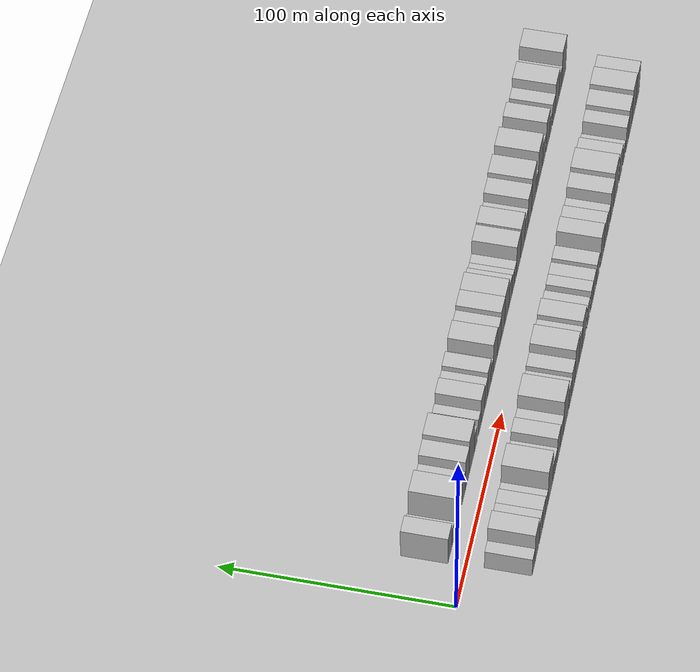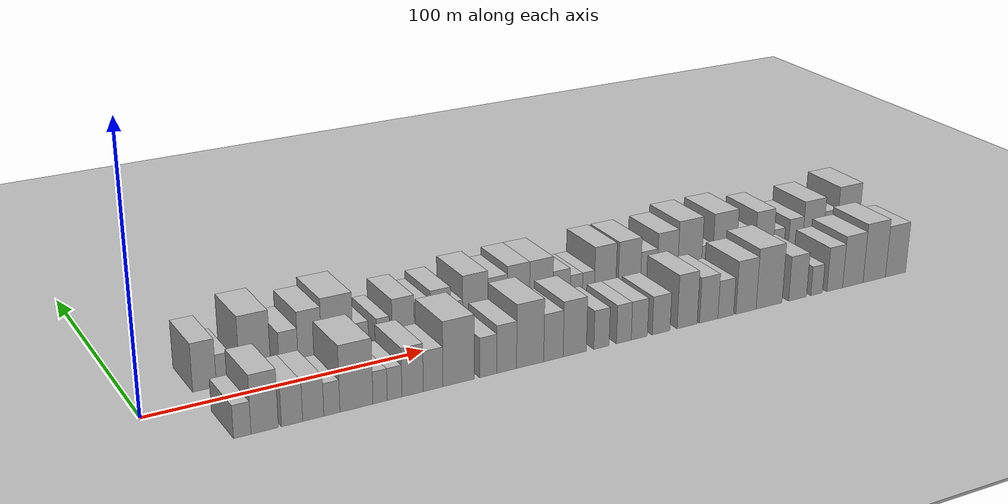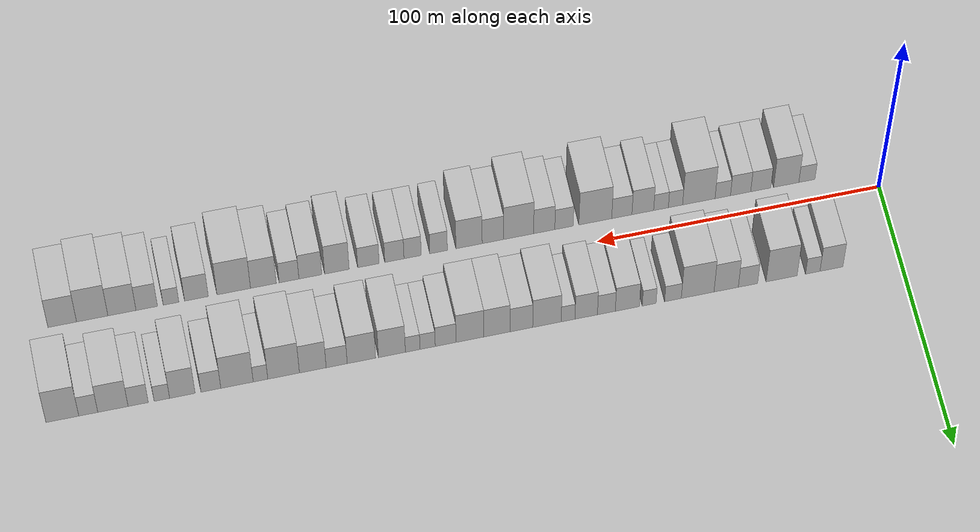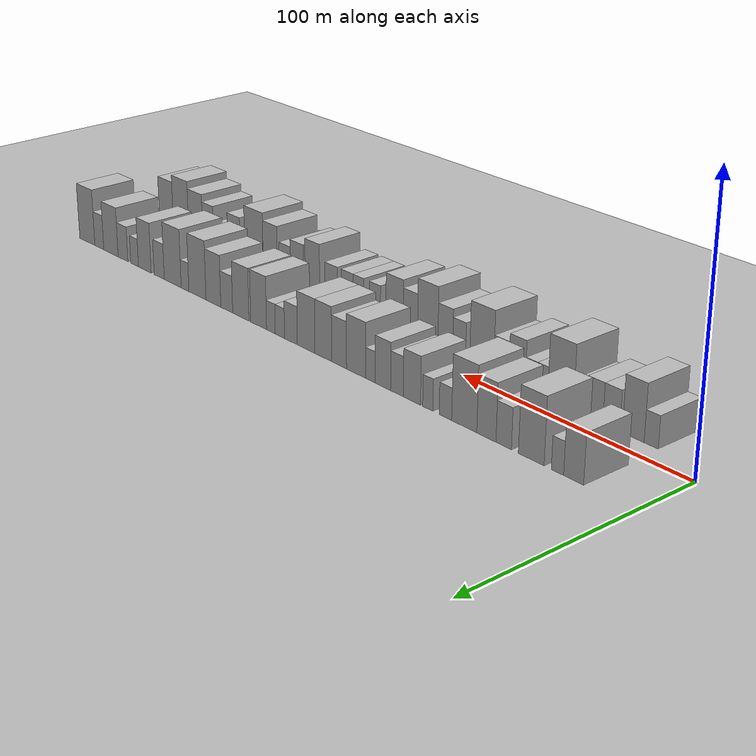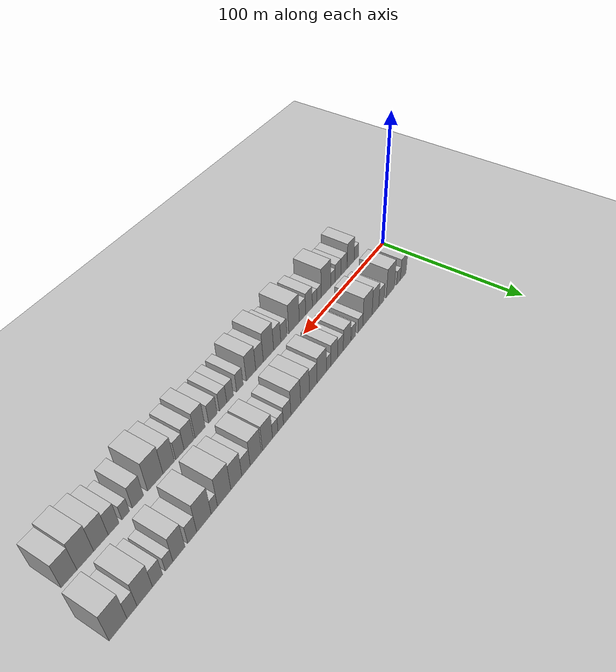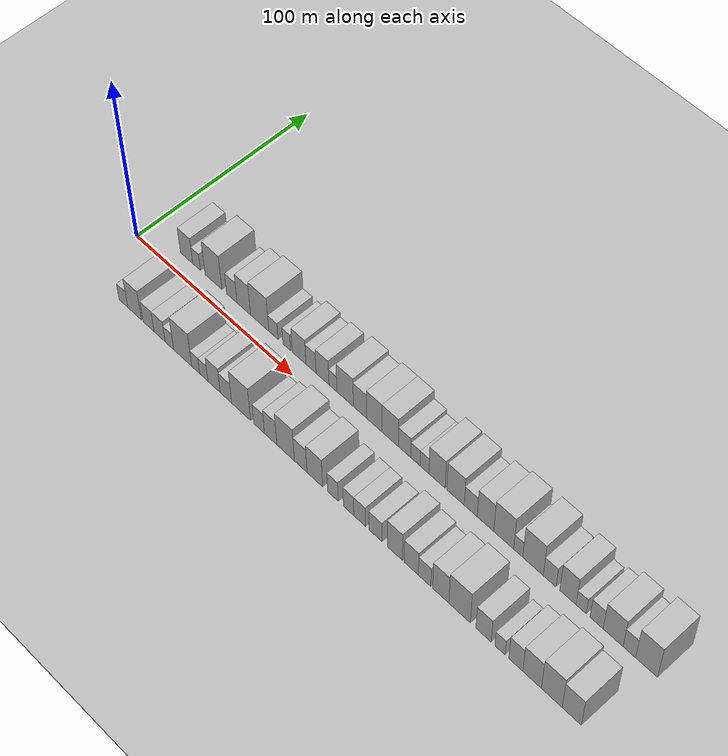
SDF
<?xml version="1.0" encoding="utf-8"?>

<sdf version="1.6">

   <world name="default">

      <gui fullscreen="0">

         <camera name="user_camera">

            <pose>-15 0 4.57585 0 0 0</pose>

            <view_controller>orbit</view_controller>

         </camera>

      </gui>

      <scene>

         <sky>

           <clouds>

             <speed>12</speed>

           </clouds>

         </sky>

         <ambient>0.4 0.4 0.4 1</ambient>

         <background>0.7 0.7 0.7 1</background>

         <shadows>1</shadows>

      </scene>

      <gravity>0 0 -9.8066</gravity>

      <magnetic_field>6e-06 2.3e-05 -4.2e-05</magnetic_field>

      <physics default="0" name="default_physics" type="ode">

         <ode>

            <solver>

               <type>quick</type>

               <iters>10</iters>

               <sor>1.0</sor>

               <use_dynamic_moi_rescaling>0</use_dynamic_moi_rescaling>

            </solver>

            <constraints>

               <cfm>0</cfm>

               <erp>0.2</erp>

               <contact_max_correcting_vel>100</contact_max_correcting_vel>

               <contact_surface_layer>0.001</contact_surface_layer>

            </constraints>

         </ode>

         <max_step_size>0.004</max_step_size>

         <real_time_factor>1</real_time_factor>

         <real_time_update_rate>250</real_time_update_rate>

      </physics>

      <light name="sun" type="directional">

         <cast_shadows>1</cast_shadows>

         <pose>0 0 10 0 0 0</pose>

         <diffuse>0.8 0.8 0.8 1</diffuse>

         <specular>0.2 0.2 0.2 1</specular>

         <attenuation>

            <range>1000</range>

            <constant>0.9</constant>

            <linear>0.01</linear>

            <quadratic>0.001</quadratic>

         </attenuation>

         <direction>-0.5 0.1 -0.9</direction>

      </light>

      <include>

         <name>ground_plane_1</name>

         <uri>model://HANNAS_ground_plane</uri>

         <pose>0 0 0  0 0 0</pose>

      </include>

      <include>

         <name>ground_plane_2</name>

         <uri>model://HANNAS_ground_plane</uri>

         <pose>100 0 0  0 0 0</pose>

      </include>

      <model name="building_1">

         <static>1</static>

         <pose frame="">24.0578 17.5000 0 0.000000 0.000000 1.570796</pose>

         <link name="link">

            <pose frame="">0 0 9.00 0 0 0</pose>

            <collision name="collision">

               <geometry>

                  <box>

                     <size>20.0000 8.1157 18.0000</size>

                  </box>

               </geometry>

               <max_contacts>10</max_contacts>

               <surface>

                  <contact>

                     <ode/>

                  </contact>

                  <bounce/>

                  <friction>

                     <torsional>

                        <ode/>

                     </torsional>

                     <ode/>

                  </friction>

               </surface>

            </collision>

            <visual name="visual">

               <cast_shadows>0</cast_shadows>

               <geometry>

                  <box>

                     <size>20.0000 8.1157 18.0000</size>

                  </box>

               </geometry>

               <material>

                  <script>

                     <uri>model://HANNAS_wall/materials/scripts</uri>

                     <uri>model://HANNAS_wall/materials/textures</uri>

                     <name>vrc/HANNAS_wall</name>

                  </script>

               </material>

            </visual>

            <self_collide>0</self_collide>

            <enable_wind>0</enable_wind>

            <kinematic>0</kinematic>

         </link>

      </model>

      <model name="building_2">

         <static>1</static>

         <pose frame="">30.6641 17.5000 0 0.000000 0.000000 1.570796</pose>

         <link name="link">

            <pose frame="">0 0 6.00 0 0 0</pose>

            <collision name="collision">

               <geometry>

                  <box>

                     <size>20.0000 5.0968 12.0000</size>

                  </box>

               </geometry>

               <max_contacts>10</max_contacts>

               <surface>

                  <contact>

                     <ode/>

                  </contact>

                  <bounce/>

                  <friction>

                     <torsional>

                        <ode/>

                     </torsional>

                     <ode/>

                  </friction>

               </surface>

            </collision>

            <visual name="visual">

               <cast_shadows>0</cast_shadows>

               <geometry>

                  <box>

                     <size>20.0000 5.0968 12.0000</size>

                  </box>

               </geometry>

               <material>

                  <script>

                     <uri>model://HANNAS_wall/materials/scripts</uri>

                     <uri>model://HANNAS_wall/materials/textures</uri>

                     <name>vrc/HANNAS_wall</name>

                  </script>

               </material>

            </visual>

            <self_collide>0</self_collide>

            <enable_wind>0</enable_wind>

            <kinematic>0</kinematic>

         </link>

      </model>

      <model name="building_3">

         <static>1</static>

         <pose frame="">41.6855 17.5000 0 0.000000 0.000000 1.570796</pose>

         <link name="link">

            <pose frame="">0 0 12.00 0 0 0</pose>

            <collision name="collision">

               <geometry>

                  <box>

                     <size>20.0000 10.9459 24.0000</size>

                  </box>

               </geometry>

               <max_contacts>10</max_contacts>

               <surface>

                  <contact>

                     <ode/>

                  </contact>

                  <bounce/>

                  <friction>

                     <torsional>

                        <ode/>

                     </torsional>

                     <ode/>

                  </friction>

               </surface>

            </collision>

            <visual name="visual">

               <cast_shadows>0</cast_shadows>

               <geometry>

                  <box>

                     <size>20.0000 10.9459 24.0000</size>

                  </box>

               </geometry>

               <material>

                  <script>

                     <uri>model://HANNAS_wall/materials/scripts</uri>

                     <uri>model://HANNAS_wall/materials/textures</uri>

                     <name>vrc/HANNAS_wall</name>

                  </script>

               </material>

            </visual>

            <self_collide>0</self_collide>

            <enable_wind>0</enable_wind>

            <kinematic>0</kinematic>

         </link>

      </model>

      <model name="building_4">

         <static>1</static>

         <pose frame="">53.5565 17.5000 0 0.000000 0.000000 1.570796</pose>

         <link name="link">

            <pose frame="">0 0 7.50 0 0 0</pose>

            <collision name="collision">

               <geometry>

                  <box>

                     <size>20.0000 6.7962 15.0000</size>

                  </box>

               </geometry>

               <max_contacts>10</max_contacts>

               <surface>

                  <contact>

                     <ode/>

                  </contact>

                  <bounce/>

                  <friction>

                     <torsional>

                        <ode/>

                     </torsional>

                     <ode/>

                  </friction>

               </surface>

            </collision>

            <visual name="visual">

               <cast_shadows>0</cast_shadows>

               <geometry>

                  <box>

                     <size>20.0000 6.7962 15.0000</size>

                  </box>

               </geometry>

               <material>

                  <script>

                     <uri>model://HANNAS_wall/materials/scripts</uri>

                     <uri>model://HANNAS_wall/materials/textures</uri>

                     <name>vrc/HANNAS_wall</name>

                  </script>

               </material>

            </visual>

            <self_collide>0</self_collide>

            <enable_wind>0</enable_wind>

            <kinematic>0</kinematic>

         </link>

      </model>

      <model name="building_5">

         <static>1</static>

         <pose frame="">61.2372 17.5000 0 0.000000 0.000000 1.570796</pose>

         <link name="link">

            <pose frame="">0 0 10.50 0 0 0</pose>

            <collision name="collision">

               <geometry>

                  <box>

                     <size>20.0000 8.5654 21.0000</size>

                  </box>

               </geometry>

               <max_contacts>10</max_contacts>

               <surface>

                  <contact>

                     <ode/>

                  </contact>

                  <bounce/>

                  <friction>

                     <torsional>

                        <ode/>

                     </torsional>

                     <ode/>

                  </friction>

               </surface>

            </collision>

            <visual name="visual">

               <cast_shadows>0</cast_shadows>

               <geometry>

                  <box>

                     <size>20.0000 8.5654 21.0000</size>

                  </box>

               </geometry>

               <material>

                  <script>

                     <uri>model://HANNAS_wall/materials/scripts</uri>

                     <uri>model://HANNAS_wall/materials/textures</uri>

                     <name>vrc/HANNAS_wall</name>

                  </script>

               </material>

            </visual>

            <self_collide>0</self_collide>

            <enable_wind>0</enable_wind>

            <kinematic>0</kinematic>

         </link>

      </model>

      <model name="building_6">

         <static>1</static>

         <pose frame="">71.2785 17.5000 0 0.000000 0.000000 1.570796</pose>

         <link name="link">

            <pose frame="">0 0 12.00 0 0 0</pose>

            <collision name="collision">

               <geometry>

                  <box>

                     <size>20.0000 11.5171 24.0000</size>

                  </box>

               </geometry>

               <max_contacts>10</max_contacts>

               <surface>

                  <contact>

                     <ode/>

                  </contact>

                  <bounce/>

                  <friction>

                     <torsional>

                        <ode/>

                     </torsional>

                     <ode/>

                  </friction>

               </surface>

            </collision>

            <visual name="visual">

               <cast_shadows>0</cast_shadows>

               <geometry>

                  <box>

                     <size>20.0000 11.5171 24.0000</size>

                  </box>

               </geometry>

               <material>

                  <script>

                     <uri>model://HANNAS_wall/materials/scripts</uri>

                     <uri>model://HANNAS_wall/materials/textures</uri>

                     <name>vrc/HANNAS_wall</name>

                  </script>

               </material>

            </visual>

            <self_collide>0</self_collide>

            <enable_wind>0</enable_wind>

            <kinematic>0</kinematic>

         </link>

      </model>

      <model name="building_7">

         <static>1</static>

         <pose frame="">79.9645 17.5000 0 0.000000 0.000000 1.570796</pose>

         <link name="link">

            <pose frame="">0 0 6.00 0 0 0</pose>

            <collision name="collision">

               <geometry>

                  <box>

                     <size>20.0000 5.8551 12.0000</size>

                  </box>

               </geometry>

               <max_contacts>10</max_contacts>

               <surface>

                  <contact>

                     <ode/>

                  </contact>

                  <bounce/>

                  <friction>

                     <torsional>

                        <ode/>

                     </torsional>

                     <ode/>

                  </friction>

               </surface>

            </collision>

            <visual name="visual">

               <cast_shadows>0</cast_shadows>

               <geometry>

                  <box>

                     <size>20.0000 5.8551 12.0000</size>

                  </box>

               </geometry>

               <material>

                  <script>

                     <uri>model://HANNAS_wall/materials/scripts</uri>

                     <uri>model://HANNAS_wall/materials/textures</uri>

                     <name>vrc/HANNAS_wall</name>

                  </script>

               </material>

            </visual>

            <self_collide>0</self_collide>

            <enable_wind>0</enable_wind>

            <kinematic>0</kinematic>

         </link>

      </model>

      <model name="building_8">

         <static>1</static>

         <pose frame="">88.3252 17.5000 0 0.000000 0.000000 1.570796</pose>

         <link name="link">

            <pose frame="">0 0 6.00 0 0 0</pose>

            <collision name="collision">

               <geometry>

                  <box>

                     <size>20.0000 4.8661 12.0000</size>

                  </box>

               </geometry>

               <max_contacts>10</max_contacts>

               <surface>

                  <contact>

                     <ode/>

                  </contact>

                  <bounce/>

                  <friction>

                     <torsional>

                        <ode/>

                     </torsional>

                     <ode/>

                  </friction>

               </surface>

            </collision>

            <visual name="visual">

               <cast_shadows>0</cast_shadows>

               <geometry>

                  <box>

                     <size>20.0000 4.8661 12.0000</size>

                  </box>

               </geometry>

               <material>

                  <script>

                     <uri>model://HANNAS_wall/materials/scripts</uri>

                     <uri>model://HANNAS_wall/materials/textures</uri>

                     <name>vrc/HANNAS_wall</name>

                  </script>

               </material>

            </visual>

            <self_collide>0</self_collide>

            <enable_wind>0</enable_wind>

            <kinematic>0</kinematic>

         </link>

      </model>

      <model name="building_9">

         <static>1</static>

         <pose frame="">95.9812 17.5000 0 0.000000 0.000000 1.570796</pose>

         <link name="link">

            <pose frame="">0 0 9.00 0 0 0</pose>

            <collision name="collision">

               <geometry>

                  <box>

                     <size>20.0000 8.4461 18.0000</size>

                  </box>

               </geometry>

               <max_contacts>10</max_contacts>

               <surface>

                  <contact>

                     <ode/>

                  </contact>

                  <bounce/>

                  <friction>

                     <torsional>

                        <ode/>

                     </torsional>

                     <ode/>

                  </friction>

               </surface>

            </collision>

            <visual name="visual">

               <cast_shadows>0</cast_shadows>

               <geometry>

                  <box>

                     <size>20.0000 8.4461 18.0000</size>

                  </box>

               </geometry>

               <material>

                  <script>

                     <uri>model://HANNAS_wall/materials/scripts</uri>

                     <uri>model://HANNAS_wall/materials/textures</uri>

                     <name>vrc/HANNAS_wall</name>

                  </script>

               </material>

            </visual>

            <self_collide>0</self_collide>

            <enable_wind>0</enable_wind>

            <kinematic>0</kinematic>

         </link>

      </model>

      <model name="building_10">

         <static>1</static>

         <pose frame="">103.3351 17.5000 0 0.000000 0.000000 1.570796</pose>

         <link name="link">

            <pose frame="">0 0 7.50 0 0 0</pose>

            <collision name="collision">

               <geometry>

                  <box>

                     <size>20.0000 6.2617 15.0000</size>

                  </box>

               </geometry>

               <max_contacts>10</max_contacts>

               <surface>

                  <contact>

                     <ode/>

                  </contact>

                  <bounce/>

                  <friction>

                     <torsional>

                        <ode/>

                     </torsional>

                     <ode/>

                  </friction>

               </surface>

            </collision>

            <visual name="visual">

               <cast_shadows>0</cast_shadows>

               <geometry>

                  <box>

                     <size>20.0000 6.2617 15.0000</size>

                  </box>

               </geometry>

               <material>

                  <script>

                     <uri>model://HANNAS_wall/materials/scripts</uri>

                     <uri>model://HANNAS_wall/materials/textures</uri>

                     <name>vrc/HANNAS_wall</name>

                  </script>

               </material>

            </visual>

            <self_collide>0</self_collide>

            <enable_wind>0</enable_wind>

            <kinematic>0</kinematic>

         </link>

      </model>

      <model name="building_11">

         <static>1</static>

         <pose frame="">110.3977 17.5000 0 0.000000 0.000000 1.570796</pose>

         <link name="link">

            <pose frame="">0 0 9.00 0 0 0</pose>

            <collision name="collision">

               <geometry>

                  <box>

                     <size>20.0000 7.8634 18.0000</size>

                  </box>

               </geometry>

               <max_contacts>10</max_contacts>

               <surface>

                  <contact>

                     <ode/>

                  </contact>

                  <bounce/>

                  <friction>

                     <torsional>

                        <ode/>

                     </torsional>

                     <ode/>

                  </friction>

               </surface>

            </collision>

            <visual name="visual">

               <cast_shadows>0</cast_shadows>

               <geometry>

                  <box>

                     <size>20.0000 7.8634 18.0000</size>

                  </box>

               </geometry>

               <material>

                  <script>

                     <uri>model://HANNAS_wall/materials/scripts</uri>

                     <uri>model://HANNAS_wall/materials/textures</uri>

                     <name>vrc/HANNAS_wall</name>

                  </script>

               </material>

            </visual>

            <self_collide>0</self_collide>

            <enable_wind>0</enable_wind>

            <kinematic>0</kinematic>

         </link>

      </model>

      <model name="building_12">

         <static>1</static>

         <pose frame="">116.7347 17.5000 0 0.000000 0.000000 1.570796</pose>

         <link name="link">

            <pose frame="">0 0 6.00 0 0 0</pose>

            <collision name="collision">

               <geometry>

                  <box>

                     <size>20.0000 4.8106 12.0000</size>

                  </box>

               </geometry>

               <max_contacts>10</max_contacts>

               <surface>

                  <contact>

                     <ode/>

                  </contact>

                  <bounce/>

                  <friction>

                     <torsional>

                        <ode/>

                     </torsional>

                     <ode/>

                  </friction>

               </surface>

            </collision>

            <visual name="visual">

               <cast_shadows>0</cast_shadows>

               <geometry>

                  <box>

                     <size>20.0000 4.8106 12.0000</size>

                  </box>

               </geometry>

               <material>

                  <script>

                     <uri>model://HANNAS_wall/materials/scripts</uri>

                     <uri>model://HANNAS_wall/materials/textures</uri>

                     <name>vrc/HANNAS_wall</name>

                  </script>

               </material>

            </visual>

            <self_collide>0</self_collide>

            <enable_wind>0</enable_wind>

            <kinematic>0</kinematic>

         </link>

      </model>

      <model name="building_13">

         <static>1</static>

         <pose frame="">124.1107 17.5000 0 0.000000 0.000000 1.570796</pose>

         <link name="link">

            <pose frame="">0 0 10.50 0 0 0</pose>

            <collision name="collision">

               <geometry>

                  <box>

                     <size>20.0000 9.9415 21.0000</size>

                  </box>

               </geometry>

               <max_contacts>10</max_contacts>

               <surface>

                  <contact>

                     <ode/>

                  </contact>

                  <bounce/>

                  <friction>

                     <torsional>

                        <ode/>

                     </torsional>

                     <ode/>

                  </friction>

               </surface>

            </collision>

            <visual name="visual">

               <cast_shadows>0</cast_shadows>

               <geometry>

                  <box>

                     <size>20.0000 9.9415 21.0000</size>

                  </box>

               </geometry>

               <material>

                  <script>

                     <uri>model://HANNAS_wall/materials/scripts</uri>

                     <uri>model://HANNAS_wall/materials/textures</uri>

                     <name>vrc/HANNAS_wall</name>

                  </script>

               </material>

            </visual>

            <self_collide>0</self_collide>

            <enable_wind>0</enable_wind>

            <kinematic>0</kinematic>

         </link>

      </model>

      <model name="building_14">

         <static>1</static>

         <pose frame="">133.0465 17.5000 0 0.000000 0.000000 1.570796</pose>

         <link name="link">

            <pose frame="">0 0 9.00 0 0 0</pose>

            <collision name="collision">

               <geometry>

                  <box>

                     <size>20.0000 7.9301 18.0000</size>

                  </box>

               </geometry>

               <max_contacts>10</max_contacts>

               <surface>

                  <contact>

                     <ode/>

                  </contact>

                  <bounce/>

                  <friction>

                     <torsional>

                        <ode/>

                     </torsional>

                     <ode/>

                  </friction>

               </surface>

            </collision>

            <visual name="visual">

               <cast_shadows>0</cast_shadows>

               <geometry>

                  <box>

                     <size>20.0000 7.9301 18.0000</size>

                  </box>

               </geometry>

               <material>

                  <script>

                     <uri>model://HANNAS_wall/materials/scripts</uri>

                     <uri>model://HANNAS_wall/materials/textures</uri>

                     <name>vrc/HANNAS_wall</name>

                  </script>

               </material>

            </visual>

            <self_collide>0</self_collide>

            <enable_wind>0</enable_wind>

            <kinematic>0</kinematic>

         </link>

      </model>

      <model name="building_15">

         <static>1</static>

         <pose frame="">141.5483 17.5000 0 0.000000 0.000000 1.570796</pose>

         <link name="link">

            <pose frame="">0 0 10.50 0 0 0</pose>

            <collision name="collision">

               <geometry>

                  <box>

                     <size>20.0000 9.0734 21.0000</size>

                  </box>

               </geometry>

               <max_contacts>10</max_contacts>

               <surface>

                  <contact>

                     <ode/>

                  </contact>

                  <bounce/>

                  <friction>

                     <torsional>

                        <ode/>

                     </torsional>

                     <ode/>

                  </friction>

               </surface>

            </collision>

            <visual name="visual">

               <cast_shadows>0</cast_shadows>

               <geometry>

                  <box>

                     <size>20.0000 9.0734 21.0000</size>

                  </box>

               </geometry>

               <material>

                  <script>

                     <uri>model://HANNAS_wall/materials/scripts</uri>

                     <uri>model://HANNAS_wall/materials/textures</uri>

                     <name>vrc/HANNAS_wall</name>

                  </script>

               </material>

            </visual>

            <self_collide>0</self_collide>

            <enable_wind>0</enable_wind>

            <kinematic>0</kinematic>

         </link>

      </model>

      <model name="building_16">

         <static>1</static>

         <pose frame="">150.9359 17.5000 0 0.000000 0.000000 1.570796</pose>

         <link name="link">

            <pose frame="">0 0 10.50 0 0 0</pose>

            <collision name="collision">

               <geometry>

                  <box>

                     <size>20.0000 9.7018 21.0000</size>

                  </box>

               </geometry>

               <max_contacts>10</max_contacts>

               <surface>

                  <contact>

                     <ode/>

                  </contact>

                  <bounce/>

                  <friction>

                     <torsional>

                        <ode/>

                     </torsional>

                     <ode/>

                  </friction>

               </surface>

            </collision>

            <visual name="visual">

               <cast_shadows>0</cast_shadows>

               <geometry>

                  <box>

                     <size>20.0000 9.7018 21.0000</size>

                  </box>

               </geometry>

               <material>

                  <script>

                     <uri>model://HANNAS_wall/materials/scripts</uri>

                     <uri>model://HANNAS_wall/materials/textures</uri>

                     <name>vrc/HANNAS_wall</name>

                  </script>

               </material>

            </visual>

            <self_collide>0</self_collide>

            <enable_wind>0</enable_wind>

            <kinematic>0</kinematic>

         </link>

      </model>

      <model name="building_17">

         <static>1</static>

         <pose frame="">159.3956 17.5000 0 0.000000 0.000000 1.570796</pose>

         <link name="link">

            <pose frame="">0 0 7.50 0 0 0</pose>

            <collision name="collision">

               <geometry>

                  <box>

                     <size>20.0000 7.2177 15.0000</size>

                  </box>

               </geometry>

               <max_contacts>10</max_contacts>

               <surface>

                  <contact>

                     <ode/>

                  </contact>

                  <bounce/>

                  <friction>

                     <torsional>

                        <ode/>

                     </torsional>

                     <ode/>

                  </friction>

               </surface>

            </collision>

            <visual name="visual">

               <cast_shadows>0</cast_shadows>

               <geometry>

                  <box>

                     <size>20.0000 7.2177 15.0000</size>

                  </box>

               </geometry>

               <material>

                  <script>

                     <uri>model://HANNAS_wall/materials/scripts</uri>

                     <uri>model://HANNAS_wall/materials/textures</uri>

                     <name>vrc/HANNAS_wall</name>

                  </script>

               </material>

            </visual>

            <self_collide>0</self_collide>

            <enable_wind>0</enable_wind>

            <kinematic>0</kinematic>

         </link>

      </model>

      <model name="building_18">

         <static>1</static>

         <pose frame="">165.6512 17.5000 0 0.000000 0.000000 1.570796</pose>

         <link name="link">

            <pose frame="">0 0 6.00 0 0 0</pose>

            <collision name="collision">

               <geometry>

                  <box>

                     <size>20.0000 5.2935 12.0000</size>

                  </box>

               </geometry>

               <max_contacts>10</max_contacts>

               <surface>

                  <contact>

                     <ode/>

                  </contact>

                  <bounce/>

                  <friction>

                     <torsional>

                        <ode/>

                     </torsional>

                     <ode/>

                  </friction>

               </surface>

            </collision>

            <visual name="visual">

               <cast_shadows>0</cast_shadows>

               <geometry>

                  <box>

                     <size>20.0000 5.2935 12.0000</size>

                  </box>

               </geometry>

               <material>

                  <script>

                     <uri>model://HANNAS_wall/materials/scripts</uri>

                     <uri>model://HANNAS_wall/materials/textures</uri>

                     <name>vrc/HANNAS_wall</name>

                  </script>

               </material>

            </visual>

            <self_collide>0</self_collide>

            <enable_wind>0</enable_wind>

            <kinematic>0</kinematic>

         </link>

      </model>

      <model name="building_19">

         <static>1</static>

         <pose frame="">170.8365 17.5000 0 0.000000 0.000000 1.570796</pose>

         <link name="link">

            <pose frame="">0 0 6.00 0 0 0</pose>

            <collision name="collision">

               <geometry>

                  <box>

                     <size>20.0000 5.0772 12.0000</size>

                  </box>

               </geometry>

               <max_contacts>10</max_contacts>

               <surface>

                  <contact>

                     <ode/>

                  </contact>

                  <bounce/>

                  <friction>

                     <torsional>

                        <ode/>

                     </torsional>

                     <ode/>

                  </friction>

               </surface>

            </collision>

            <visual name="visual">

               <cast_shadows>0</cast_shadows>

               <geometry>

                  <box>

                     <size>20.0000 5.0772 12.0000</size>

                  </box>

               </geometry>

               <material>

                  <script>

                     <uri>model://HANNAS_wall/materials/scripts</uri>

                     <uri>model://HANNAS_wall/materials/textures</uri>

                     <name>vrc/HANNAS_wall</name>

                  </script>

               </material>

            </visual>

            <self_collide>0</self_collide>

            <enable_wind>0</enable_wind>

            <kinematic>0</kinematic>

         </link>

      </model>

      <model name="building_20">

         <static>1</static>

         <pose frame="">178.0342 17.5000 0 0.000000 0.000000 1.570796</pose>

         <link name="link">

            <pose frame="">0 0 10.50 0 0 0</pose>

            <collision name="collision">

               <geometry>

                  <box>

                     <size>20.0000 9.3181 21.0000</size>

                  </box>

               </geometry>

               <max_contacts>10</max_contacts>

               <surface>

                  <contact>

                     <ode/>

                  </contact>

                  <bounce/>

                  <friction>

                     <torsional>

                        <ode/>

                     </torsional>

                     <ode/>

                  </friction>

               </surface>

            </collision>

            <visual name="visual">

               <cast_shadows>0</cast_shadows>

               <geometry>

                  <box>

                     <size>20.0000 9.3181 21.0000</size>

                  </box>

               </geometry>

               <material>

                  <script>

                     <uri>model://HANNAS_wall/materials/scripts</uri>

                     <uri>model://HANNAS_wall/materials/textures</uri>

                     <name>vrc/HANNAS_wall</name>

                  </script>

               </material>

            </visual>

            <self_collide>0</self_collide>

            <enable_wind>0</enable_wind>

            <kinematic>0</kinematic>

         </link>

      </model>

      <model name="building_21">

         <static>1</static>

         <pose frame="">188.6076 17.5000 0 0.000000 0.000000 1.570796</pose>

         <link name="link">

            <pose frame="">0 0 10.50 0 0 0</pose>

            <collision name="collision">

               <geometry>

                  <box>

                     <size>20.0000 9.8288 21.0000</size>

                  </box>

               </geometry>

               <max_contacts>10</max_contacts>

               <surface>

                  <contact>

                     <ode/>

                  </contact>

                  <bounce/>

                  <friction>

                     <torsional>

                        <ode/>

                     </torsional>

                     <ode/>

                  </friction>

               </surface>

            </collision>

            <visual name="visual">

               <cast_shadows>0</cast_shadows>

               <geometry>

                  <box>

                     <size>20.0000 9.8288 21.0000</size>

                  </box>

               </geometry>

               <material>

                  <script>

                     <uri>model://HANNAS_wall/materials/scripts</uri>

                     <uri>model://HANNAS_wall/materials/textures</uri>

                     <name>vrc/HANNAS_wall</name>

                  </script>

               </material>

            </visual>

            <self_collide>0</self_collide>

            <enable_wind>0</enable_wind>

            <kinematic>0</kinematic>

         </link>

      </model>

      <model name="building_22">

         <static>1</static>

         <pose frame="">197.1594 17.5000 0 0.000000 0.000000 1.570796</pose>

         <link name="link">

            <pose frame="">0 0 7.50 0 0 0</pose>

            <collision name="collision">

               <geometry>

                  <box>

                     <size>20.0000 7.2749 15.0000</size>

                  </box>

               </geometry>

               <max_contacts>10</max_contacts>

               <surface>

                  <contact>

                     <ode/>

                  </contact>

                  <bounce/>

                  <friction>

                     <torsional>

                        <ode/>

                     </torsional>

                     <ode/>

                  </friction>

               </surface>

            </collision>

            <visual name="visual">

               <cast_shadows>0</cast_shadows>

               <geometry>

                  <box>

                     <size>20.0000 7.2749 15.0000</size>

                  </box>

               </geometry>

               <material>

                  <script>

                     <uri>model://HANNAS_wall/materials/scripts</uri>

                     <uri>model://HANNAS_wall/materials/textures</uri>

                     <name>vrc/HANNAS_wall</name>

                  </script>

               </material>

            </visual>

            <self_collide>0</self_collide>

            <enable_wind>0</enable_wind>

            <kinematic>0</kinematic>

         </link>

      </model>

      <model name="building_23">

         <static>1</static>

         <pose frame="">205.4156 17.5000 0 0.000000 0.000000 1.570796</pose>

         <link name="link">

            <pose frame="">0 0 10.50 0 0 0</pose>

            <collision name="collision">

               <geometry>

                  <box>

                     <size>20.0000 9.2373 21.0000</size>

                  </box>

               </geometry>

               <max_contacts>10</max_contacts>

               <surface>

                  <contact>

                     <ode/>

                  </contact>

                  <bounce/>

                  <friction>

                     <torsional>

                        <ode/>

                     </torsional>

                     <ode/>

                  </friction>

               </surface>

            </collision>

            <visual name="visual">

               <cast_shadows>0</cast_shadows>

               <geometry>

                  <box>

                     <size>20.0000 9.2373 21.0000</size>

                  </box>

               </geometry>

               <material>

                  <script>

                     <uri>model://HANNAS_wall/materials/scripts</uri>

                     <uri>model://HANNAS_wall/materials/textures</uri>

                     <name>vrc/HANNAS_wall</name>

                  </script>

               </material>

            </visual>

            <self_collide>0</self_collide>

            <enable_wind>0</enable_wind>

            <kinematic>0</kinematic>

         </link>

      </model>

      <model name="building_24">

         <static>1</static>

         <pose frame="">215.4934 17.5000 0 0.000000 0.000000 1.570796</pose>

         <link name="link">

            <pose frame="">0 0 12.00 0 0 0</pose>

            <collision name="collision">

               <geometry>

                  <box>

                     <size>20.0000 10.9183 24.0000</size>

                  </box>

               </geometry>

               <max_contacts>10</max_contacts>

               <surface>

                  <contact>

                     <ode/>

                  </contact>

                  <bounce/>

                  <friction>

                     <torsional>

                        <ode/>

                     </torsional>

                     <ode/>

                  </friction>

               </surface>

            </collision>

            <visual name="visual">

               <cast_shadows>0</cast_shadows>

               <geometry>

                  <box>

                     <size>20.0000 10.9183 24.0000</size>

                  </box>

               </geometry>

               <material>

                  <script>

                     <uri>model://HANNAS_wall/materials/scripts</uri>

                     <uri>model://HANNAS_wall/materials/textures</uri>

                     <name>vrc/HANNAS_wall</name>

                  </script>

               </material>

            </visual>

            <self_collide>0</self_collide>

            <enable_wind>0</enable_wind>

            <kinematic>0</kinematic>

         </link>

      </model>

      <model name="building_25">

         <static>1</static>

         <pose frame="">223.4560 17.5000 0 0.000000 0.000000 1.570796</pose>

         <link name="link">

            <pose frame="">0 0 6.00 0 0 0</pose>

            <collision name="collision">

               <geometry>

                  <box>

                     <size>20.0000 5.0069 12.0000</size>

                  </box>

               </geometry>

               <max_contacts>10</max_contacts>

               <surface>

                  <contact>

                     <ode/>

                  </contact>

                  <bounce/>

                  <friction>

                     <torsional>

                        <ode/>

                     </torsional>

                     <ode/>

                  </friction>

               </surface>

            </collision>

            <visual name="visual">

               <cast_shadows>0</cast_shadows>

               <geometry>

                  <box>

                     <size>20.0000 5.0069 12.0000</size>

                  </box>

               </geometry>

               <material>

                  <script>

                     <uri>model://HANNAS_wall/materials/scripts</uri>

                     <uri>model://HANNAS_wall/materials/textures</uri>

                     <name>vrc/HANNAS_wall</name>

                  </script>

               </material>

            </visual>

            <self_collide>0</self_collide>

            <enable_wind>0</enable_wind>

            <kinematic>0</kinematic>

         </link>

      </model>

      <model name="building_26">

         <static>1</static>

         <pose frame="">231.5347 17.5000 0 0.000000 0.000000 1.570796</pose>

         <link name="link">

            <pose frame="">0 0 12.00 0 0 0</pose>

            <collision name="collision">

               <geometry>

                  <box>

                     <size>20.0000 11.1506 24.0000</size>

                  </box>

               </geometry>

               <max_contacts>10</max_contacts>

               <surface>

                  <contact>

                     <ode/>

                  </contact>

                  <bounce/>

                  <friction>

                     <torsional>

                        <ode/>

                     </torsional>

                     <ode/>

                  </friction>

               </surface>

            </collision>

            <visual name="visual">

               <cast_shadows>0</cast_shadows>

               <geometry>

                  <box>

                     <size>20.0000 11.1506 24.0000</size>

                  </box>

               </geometry>

               <material>

                  <script>

                     <uri>model://HANNAS_wall/materials/scripts</uri>

                     <uri>model://HANNAS_wall/materials/textures</uri>

                     <name>vrc/HANNAS_wall</name>

                  </script>

               </material>

            </visual>

            <self_collide>0</self_collide>

            <enable_wind>0</enable_wind>

            <kinematic>0</kinematic>

         </link>

      </model>

      <model name="building_27">

         <static>1</static>

         <pose frame="">240.5277 17.5000 0 0.000000 0.000000 1.570796</pose>

         <link name="link">

            <pose frame="">0 0 7.50 0 0 0</pose>

            <collision name="collision">

               <geometry>

                  <box>

                     <size>20.0000 6.8353 15.0000</size>

                  </box>

               </geometry>

               <max_contacts>10</max_contacts>

               <surface>

                  <contact>

                     <ode/>

                  </contact>

                  <bounce/>

                  <friction>

                     <torsional>

                        <ode/>

                     </torsional>

                     <ode/>

                  </friction>

               </surface>

            </collision>

            <visual name="visual">

               <cast_shadows>0</cast_shadows>

               <geometry>

                  <box>

                     <size>20.0000 6.8353 15.0000</size>

                  </box>

               </geometry>

               <material>

                  <script>

                     <uri>model://HANNAS_wall/materials/scripts</uri>

                     <uri>model://HANNAS_wall/materials/textures</uri>

                     <name>vrc/HANNAS_wall</name>

                  </script>

               </material>

            </visual>

            <self_collide>0</self_collide>

            <enable_wind>0</enable_wind>

            <kinematic>0</kinematic>

         </link>

      </model>

      <model name="building_28">

         <static>1</static>

         <pose frame="">250.3241 17.5000 0 0.000000 0.000000 1.570796</pose>

         <link name="link">

            <pose frame="">0 0 10.50 0 0 0</pose>

            <collision name="collision">

               <geometry>

                  <box>

                     <size>20.0000 8.7576 21.0000</size>

                  </box>

               </geometry>

               <max_contacts>10</max_contacts>

               <surface>

                  <contact>

                     <ode/>

                  </contact>

                  <bounce/>

                  <friction>

                     <torsional>

                        <ode/>

                     </torsional>

                     <ode/>

                  </friction>

               </surface>

            </collision>

            <visual name="visual">

               <cast_shadows>0</cast_shadows>

               <geometry>

                  <box>

                     <size>20.0000 8.7576 21.0000</size>

                  </box>

               </geometry>

               <material>

                  <script>

                     <uri>model://HANNAS_wall/materials/scripts</uri>

                     <uri>model://HANNAS_wall/materials/textures</uri>

                     <name>vrc/HANNAS_wall</name>

                  </script>

               </material>

            </visual>

            <self_collide>0</self_collide>

            <enable_wind>0</enable_wind>

            <kinematic>0</kinematic>

         </link>

      </model>

      <model name="building_29">

         <static>1</static>

         <pose frame="">257.3588 17.5000 0 0.000000 0.000000 1.570796</pose>

         <link name="link">

            <pose frame="">0 0 6.00 0 0 0</pose>

            <collision name="collision">

               <geometry>

                  <box>

                     <size>20.0000 5.3117 12.0000</size>

                  </box>

               </geometry>

               <max_contacts>10</max_contacts>

               <surface>

                  <contact>

                     <ode/>

                  </contact>

                  <bounce/>

                  <friction>

                     <torsional>

                        <ode/>

                     </torsional>

                     <ode/>

                  </friction>

               </surface>

            </collision>

            <visual name="visual">

               <cast_shadows>0</cast_shadows>

               <geometry>

                  <box>

                     <size>20.0000 5.3117 12.0000</size>

                  </box>

               </geometry>

               <material>

                  <script>

                     <uri>model://HANNAS_wall/materials/scripts</uri>

                     <uri>model://HANNAS_wall/materials/textures</uri>

                     <name>vrc/HANNAS_wall</name>

                  </script>

               </material>

            </visual>

            <self_collide>0</self_collide>

            <enable_wind>0</enable_wind>

            <kinematic>0</kinematic>

         </link>

      </model>

      <model name="building_30">

         <static>1</static>

         <pose frame="">265.4738 17.5000 0 0.000000 0.000000 1.570796</pose>

         <link name="link">

            <pose frame="">0 0 7.50 0 0 0</pose>

            <collision name="collision">

               <geometry>

                  <box>

                     <size>20.0000 6.9183 15.0000</size>

                  </box>

               </geometry>

               <max_contacts>10</max_contacts>

               <surface>

                  <contact>

                     <ode/>

                  </contact>

                  <bounce/>

                  <friction>

                     <torsional>

                        <ode/>

                     </torsional>

                     <ode/>

                  </friction>

               </surface>

            </collision>

            <visual name="visual">

               <cast_shadows>0</cast_shadows>

               <geometry>

                  <box>

                     <size>20.0000 6.9183 15.0000</size>

                  </box>

               </geometry>

               <material>

                  <script>

                     <uri>model://HANNAS_wall/materials/scripts</uri>

                     <uri>model://HANNAS_wall/materials/textures</uri>

                     <name>vrc/HANNAS_wall</name>

                  </script>

               </material>

            </visual>

            <self_collide>0</self_collide>

            <enable_wind>0</enable_wind>

            <kinematic>0</kinematic>

         </link>

      </model>

      <model name="building_31">

         <static>1</static>

         <pose frame="">274.1179 17.5000 0 0.000000 0.000000 1.570796</pose>

         <link name="link">

            <pose frame="">0 0 10.50 0 0 0</pose>

            <collision name="collision">

               <geometry>

                  <box>

                     <size>20.0000 10.3699 21.0000</size>

                  </box>

               </geometry>

               <max_contacts>10</max_contacts>

               <surface>

                  <contact>

                     <ode/>

                  </contact>

                  <bounce/>

                  <friction>

                     <torsional>

                        <ode/>

                     </torsional>

                     <ode/>

                  </friction>

               </surface>

            </collision>

            <visual name="visual">

               <cast_shadows>0</cast_shadows>

               <geometry>

                  <box>

                     <size>20.0000 10.3699 21.0000</size>

                  </box>

               </geometry>

               <material>

                  <script>

                     <uri>model://HANNAS_wall/materials/scripts</uri>

                     <uri>model://HANNAS_wall/materials/textures</uri>

                     <name>vrc/HANNAS_wall</name>

                  </script>

               </material>

            </visual>

            <self_collide>0</self_collide>

            <enable_wind>0</enable_wind>

            <kinematic>0</kinematic>

         </link>

      </model>

      <model name="building_32">

         <static>1</static>

         <pose frame="">282.5498 17.5000 0 0.000000 0.000000 1.570796</pose>

         <link name="link">

            <pose frame="">0 0 7.50 0 0 0</pose>

            <collision name="collision">

               <geometry>

                  <box>

                     <size>20.0000 6.4940 15.0000</size>

                  </box>

               </geometry>

               <max_contacts>10</max_contacts>

               <surface>

                  <contact>

                     <ode/>

                  </contact>

                  <bounce/>

                  <friction>

                     <torsional>

                        <ode/>

                     </torsional>

                     <ode/>

                  </friction>

               </surface>

            </collision>

            <visual name="visual">

               <cast_shadows>0</cast_shadows>

               <geometry>

                  <box>

                     <size>20.0000 6.4940 15.0000</size>

                  </box>

               </geometry>

               <material>

                  <script>

                     <uri>model://HANNAS_wall/materials/scripts</uri>

                     <uri>model://HANNAS_wall/materials/textures</uri>

                     <name>vrc/HANNAS_wall</name>

                  </script>

               </material>

            </visual>

            <self_collide>0</self_collide>

            <enable_wind>0</enable_wind>

            <kinematic>0</kinematic>

         </link>

      </model>

      <model name="building_33">

         <static>1</static>

         <pose frame="">291.4009 17.5000 0 0.000000 0.000000 1.570796</pose>

         <link name="link">

            <pose frame="">0 0 12.00 0 0 0</pose>

            <collision name="collision">

               <geometry>

                  <box>

                     <size>20.0000 11.2081 24.0000</size>

                  </box>

               </geometry>

               <max_contacts>10</max_contacts>

               <surface>

                  <contact>

                     <ode/>

                  </contact>

                  <bounce/>

                  <friction>

                     <torsional>

                        <ode/>

                     </torsional>

                     <ode/>

                  </friction>

               </surface>

            </collision>

            <visual name="visual">

               <cast_shadows>0</cast_shadows>

               <geometry>

                  <box>

                     <size>20.0000 11.2081 24.0000</size>

                  </box>

               </geometry>

               <material>

                  <script>

                     <uri>model://HANNAS_wall/materials/scripts</uri>

                     <uri>model://HANNAS_wall/materials/textures</uri>

                     <name>vrc/HANNAS_wall</name>

                  </script>

               </material>

            </visual>

            <self_collide>0</self_collide>

            <enable_wind>0</enable_wind>

            <kinematic>0</kinematic>

         </link>

      </model>

      <model name="building_34">

         <static>1</static>

         <pose frame="">23.8735 -17.5000 0 0.000000 0.000000 1.570796</pose>

         <link name="link">

            <pose frame="">0 0 6.00 0 0 0</pose>

            <collision name="collision">

               <geometry>

                  <box>

                     <size>20.0000 5.7471 12.0000</size>

                  </box>

               </geometry>

               <max_contacts>10</max_contacts>

               <surface>

                  <contact>

                     <ode/>

                  </contact>

                  <bounce/>

                  <friction>

                     <torsional>

                        <ode/>

                     </torsional>

                     <ode/>

                  </friction>

               </surface>

            </collision>

            <visual name="visual">

               <cast_shadows>0</cast_shadows>

               <geometry>

                  <box>

                     <size>20.0000 5.7471 12.0000</size>

                  </box>

               </geometry>

               <material>

                  <script>

                     <uri>model://HANNAS_wall/materials/scripts</uri>

                     <uri>model://HANNAS_wall/materials/textures</uri>

                     <name>vrc/HANNAS_wall</name>

                  </script>

               </material>

            </visual>

            <self_collide>0</self_collide>

            <enable_wind>0</enable_wind>

            <kinematic>0</kinematic>

         </link>

      </model>

      <model name="building_35">

         <static>1</static>

         <pose frame="">31.2713 -17.5000 0 0.000000 0.000000 1.570796</pose>

         <link name="link">

            <pose frame="">0 0 10.50 0 0 0</pose>

            <collision name="collision">

               <geometry>

                  <box>

                     <size>20.0000 9.0483 21.0000</size>

                  </box>

               </geometry>

               <max_contacts>10</max_contacts>

               <surface>

                  <contact>

                     <ode/>

                  </contact>

                  <bounce/>

                  <friction>

                     <torsional>

                        <ode/>

                     </torsional>

                     <ode/>

                  </friction>

               </surface>

            </collision>

            <visual name="visual">

               <cast_shadows>0</cast_shadows>

               <geometry>

                  <box>

                     <size>20.0000 9.0483 21.0000</size>

                  </box>

               </geometry>

               <material>

                  <script>

                     <uri>model://HANNAS_wall/materials/scripts</uri>

                     <uri>model://HANNAS_wall/materials/textures</uri>

                     <name>vrc/HANNAS_wall</name>

                  </script>

               </material>

            </visual>

            <self_collide>0</self_collide>

            <enable_wind>0</enable_wind>

            <kinematic>0</kinematic>

         </link>

      </model>

      <model name="building_36">

         <static>1</static>

         <pose frame="">40.3777 -17.5000 0 0.000000 0.000000 1.570796</pose>

         <link name="link">

            <pose frame="">0 0 7.50 0 0 0</pose>

            <collision name="collision">

               <geometry>

                  <box>

                     <size>20.0000 7.1645 15.0000</size>

                  </box>

               </geometry>

               <max_contacts>10</max_contacts>

               <surface>

                  <contact>

                     <ode/>

                  </contact>

                  <bounce/>

                  <friction>

                     <torsional>

                        <ode/>

                     </torsional>

                     <ode/>

                  </friction>

               </surface>

            </collision>

            <visual name="visual">

               <cast_shadows>0</cast_shadows>

               <geometry>

                  <box>

                     <size>20.0000 7.1645 15.0000</size>

                  </box>

               </geometry>

               <material>

                  <script>

                     <uri>model://HANNAS_wall/materials/scripts</uri>

                     <uri>model://HANNAS_wall/materials/textures</uri>

                     <name>vrc/HANNAS_wall</name>

                  </script>

               </material>

            </visual>

            <self_collide>0</self_collide>

            <enable_wind>0</enable_wind>

            <kinematic>0</kinematic>

         </link>

      </model>

      <model name="building_37">

         <static>1</static>

         <pose frame="">47.5649 -17.5000 0 0.000000 0.000000 1.570796</pose>

         <link name="link">

            <pose frame="">0 0 7.50 0 0 0</pose>

            <collision name="collision">

               <geometry>

                  <box>

                     <size>20.0000 7.2100 15.0000</size>

                  </box>

               </geometry>

               <max_contacts>10</max_contacts>

               <surface>

                  <contact>

                     <ode/>

                  </contact>

                  <bounce/>

                  <friction>

                     <torsional>

                        <ode/>

                     </torsional>

                     <ode/>

                  </friction>

               </surface>

            </collision>

            <visual name="visual">

               <cast_shadows>0</cast_shadows>

               <geometry>

                  <box>

                     <size>20.0000 7.2100 15.0000</size>

                  </box>

               </geometry>

               <material>

                  <script>

                     <uri>model://HANNAS_wall/materials/scripts</uri>

                     <uri>model://HANNAS_wall/materials/textures</uri>

                     <name>vrc/HANNAS_wall</name>

                  </script>

               </material>

            </visual>

            <self_collide>0</self_collide>

            <enable_wind>0</enable_wind>

            <kinematic>0</kinematic>

         </link>

      </model>

      <model name="building_38">

         <static>1</static>

         <pose frame="">53.9277 -17.5000 0 0.000000 0.000000 1.570796</pose>

         <link name="link">

            <pose frame="">0 0 6.00 0 0 0</pose>

            <collision name="collision">

               <geometry>

                  <box>

                     <size>20.0000 5.5156 12.0000</size>

                  </box>

               </geometry>

               <max_contacts>10</max_contacts>

               <surface>

                  <contact>

                     <ode/>

                  </contact>

                  <bounce/>

                  <friction>

                     <torsional>

                        <ode/>

                     </torsional>

                     <ode/>

                  </friction>

               </surface>

            </collision>

            <visual name="visual">

               <cast_shadows>0</cast_shadows>

               <geometry>

                  <box>

                     <size>20.0000 5.5156 12.0000</size>

                  </box>

               </geometry>

               <material>

                  <script>

                     <uri>model://HANNAS_wall/materials/scripts</uri>

                     <uri>model://HANNAS_wall/materials/textures</uri>

                     <name>vrc/HANNAS_wall</name>

                  </script>

               </material>

            </visual>

            <self_collide>0</self_collide>

            <enable_wind>0</enable_wind>

            <kinematic>0</kinematic>

         </link>

      </model>

      <model name="building_39">

         <static>1</static>

         <pose frame="">62.4632 -17.5000 0 0.000000 0.000000 1.570796</pose>

         <link name="link">

            <pose frame="">0 0 12.00 0 0 0</pose>

            <collision name="collision">

               <geometry>

                  <box>

                     <size>20.0000 11.5554 24.0000</size>

                  </box>

               </geometry>

               <max_contacts>10</max_contacts>

               <surface>

                  <contact>

                     <ode/>

                  </contact>

                  <bounce/>

                  <friction>

                     <torsional>

                        <ode/>

                     </torsional>

                     <ode/>

                  </friction>

               </surface>

            </collision>

            <visual name="visual">

               <cast_shadows>0</cast_shadows>

               <geometry>

                  <box>

                     <size>20.0000 11.5554 24.0000</size>

                  </box>

               </geometry>

               <material>

                  <script>

                     <uri>model://HANNAS_wall/materials/scripts</uri>

                     <uri>model://HANNAS_wall/materials/textures</uri>

                     <name>vrc/HANNAS_wall</name>

                  </script>

               </material>

            </visual>

            <self_collide>0</self_collide>

            <enable_wind>0</enable_wind>

            <kinematic>0</kinematic>

         </link>

      </model>

      <model name="building_40">

         <static>1</static>

         <pose frame="">70.7656 -17.5000 0 0.000000 0.000000 1.570796</pose>

         <link name="link">

            <pose frame="">0 0 6.00 0 0 0</pose>

            <collision name="collision">

               <geometry>

                  <box>

                     <size>20.0000 5.0493 12.0000</size>

                  </box>

               </geometry>

               <max_contacts>10</max_contacts>

               <surface>

                  <contact>

                     <ode/>

                  </contact>

                  <bounce/>

                  <friction>

                     <torsional>

                        <ode/>

                     </torsional>

                     <ode/>

                  </friction>

               </surface>

            </collision>

            <visual name="visual">

               <cast_shadows>0</cast_shadows>

               <geometry>

                  <box>

                     <size>20.0000 5.0493 12.0000</size>

                  </box>

               </geometry>

               <material>

                  <script>

                     <uri>model://HANNAS_wall/materials/scripts</uri>

                     <uri>model://HANNAS_wall/materials/textures</uri>

                     <name>vrc/HANNAS_wall</name>

                  </script>

               </material>

            </visual>

            <self_collide>0</self_collide>

            <enable_wind>0</enable_wind>

            <kinematic>0</kinematic>

         </link>

      </model>

      <model name="building_41">

         <static>1</static>

         <pose frame="">75.9027 -17.5000 0 0.000000 0.000000 1.570796</pose>

         <link name="link">

            <pose frame="">0 0 6.00 0 0 0</pose>

            <collision name="collision">

               <geometry>

                  <box>

                     <size>20.0000 5.2249 12.0000</size>

                  </box>

               </geometry>

               <max_contacts>10</max_contacts>

               <surface>

                  <contact>

                     <ode/>

                  </contact>

                  <bounce/>

                  <friction>

                     <torsional>

                        <ode/>

                     </torsional>

                     <ode/>

                  </friction>

               </surface>

            </collision>

            <visual name="visual">

               <cast_shadows>0</cast_shadows>

               <geometry>

                  <box>

                     <size>20.0000 5.2249 12.0000</size>

                  </box>

               </geometry>

               <material>

                  <script>

                     <uri>model://HANNAS_wall/materials/scripts</uri>

                     <uri>model://HANNAS_wall/materials/textures</uri>

                     <name>vrc/HANNAS_wall</name>

                  </script>

               </material>

            </visual>

            <self_collide>0</self_collide>

            <enable_wind>0</enable_wind>

            <kinematic>0</kinematic>

         </link>

      </model>

      <model name="building_42">

         <static>1</static>

         <pose frame="">82.3749 -17.5000 0 0.000000 0.000000 1.570796</pose>

         <link name="link">

            <pose frame="">0 0 9.00 0 0 0</pose>

            <collision name="collision">

               <geometry>

                  <box>

                     <size>20.0000 7.7195 18.0000</size>

                  </box>

               </geometry>

               <max_contacts>10</max_contacts>

               <surface>

                  <contact>

                     <ode/>

                  </contact>

                  <bounce/>

                  <friction>

                     <torsional>

                        <ode/>

                     </torsional>

                     <ode/>

                  </friction>

               </surface>

            </collision>

            <visual name="visual">

               <cast_shadows>0</cast_shadows>

               <geometry>

                  <box>

                     <size>20.0000 7.7195 18.0000</size>

                  </box>

               </geometry>

               <material>

                  <script>

                     <uri>model://HANNAS_wall/materials/scripts</uri>

                     <uri>model://HANNAS_wall/materials/textures</uri>

                     <name>vrc/HANNAS_wall</name>

                  </script>

               </material>

            </visual>

            <self_collide>0</self_collide>

            <enable_wind>0</enable_wind>

            <kinematic>0</kinematic>

         </link>

      </model>

      <model name="building_43">

         <static>1</static>

         <pose frame="">89.8142 -17.5000 0 0.000000 0.000000 1.570796</pose>

         <link name="link">

            <pose frame="">0 0 7.50 0 0 0</pose>

            <collision name="collision">

               <geometry>

                  <box>

                     <size>20.0000 7.1592 15.0000</size>

                  </box>

               </geometry>

               <max_contacts>10</max_contacts>

               <surface>

                  <contact>

                     <ode/>

                  </contact>

                  <bounce/>

                  <friction>

                     <torsional>

                        <ode/>

                     </torsional>

                     <ode/>

                  </friction>

               </surface>

            </collision>

            <visual name="visual">

               <cast_shadows>0</cast_shadows>

               <geometry>

                  <box>

                     <size>20.0000 7.1592 15.0000</size>

                  </box>

               </geometry>

               <material>

                  <script>

                     <uri>model://HANNAS_wall/materials/scripts</uri>

                     <uri>model://HANNAS_wall/materials/textures</uri>

                     <name>vrc/HANNAS_wall</name>

                  </script>

               </material>

            </visual>

            <self_collide>0</self_collide>

            <enable_wind>0</enable_wind>

            <kinematic>0</kinematic>

         </link>

      </model>

      <model name="building_44">

         <static>1</static>

         <pose frame="">99.2130 -17.5000 0 0.000000 0.000000 1.570796</pose>

         <link name="link">

            <pose frame="">0 0 12.00 0 0 0</pose>

            <collision name="collision">

               <geometry>

                  <box>

                     <size>20.0000 11.6384 24.0000</size>

                  </box>

               </geometry>

               <max_contacts>10</max_contacts>

               <surface>

                  <contact>

                     <ode/>

                  </contact>

                  <bounce/>

                  <friction>

                     <torsional>

                        <ode/>

                     </torsional>

                     <ode/>

                  </friction>

               </surface>

            </collision>

            <visual name="visual">

               <cast_shadows>0</cast_shadows>

               <geometry>

                  <box>

                     <size>20.0000 11.6384 24.0000</size>

                  </box>

               </geometry>

               <material>

                  <script>

                     <uri>model://HANNAS_wall/materials/scripts</uri>

                     <uri>model://HANNAS_wall/materials/textures</uri>

                     <name>vrc/HANNAS_wall</name>

                  </script>

               </material>

            </visual>

            <self_collide>0</self_collide>

            <enable_wind>0</enable_wind>

            <kinematic>0</kinematic>

         </link>

      </model>

      <model name="building_45">

         <static>1</static>

         <pose frame="">110.2833 -17.5000 0 0.000000 0.000000 1.570796</pose>

         <link name="link">

            <pose frame="">0 0 7.50 0 0 0</pose>

            <collision name="collision">

               <geometry>

                  <box>

                     <size>20.0000 6.5022 15.0000</size>

                  </box>

               </geometry>

               <max_contacts>10</max_contacts>

               <surface>

                  <contact>

                     <ode/>

                  </contact>

                  <bounce/>

                  <friction>

                     <torsional>

                        <ode/>

                     </torsional>

                     <ode/>

                  </friction>

               </surface>

            </collision>

            <visual name="visual">

               <cast_shadows>0</cast_shadows>

               <geometry>

                  <box>

                     <size>20.0000 6.5022 15.0000</size>

                  </box>

               </geometry>

               <material>

                  <script>

                     <uri>model://HANNAS_wall/materials/scripts</uri>

                     <uri>model://HANNAS_wall/materials/textures</uri>

                     <name>vrc/HANNAS_wall</name>

                  </script>

               </material>

            </visual>

            <self_collide>0</self_collide>

            <enable_wind>0</enable_wind>

            <kinematic>0</kinematic>

         </link>

      </model>

      <model name="building_46">

         <static>1</static>

         <pose frame="">117.2811 -17.5000 0 0.000000 0.000000 1.570796</pose>

         <link name="link">

            <pose frame="">0 0 9.00 0 0 0</pose>

            <collision name="collision">

               <geometry>

                  <box>

                     <size>20.0000 7.4935 18.0000</size>

                  </box>

               </geometry>

               <max_contacts>10</max_contacts>

               <surface>

                  <contact>

                     <ode/>

                  </contact>

                  <bounce/>

                  <friction>

                     <torsional>

                        <ode/>

                     </torsional>

                     <ode/>

                  </friction>

               </surface>

            </collision>

            <visual name="visual">

               <cast_shadows>0</cast_shadows>

               <geometry>

                  <box>

                     <size>20.0000 7.4935 18.0000</size>

                  </box>

               </geometry>

               <material>

                  <script>

                     <uri>model://HANNAS_wall/materials/scripts</uri>

                     <uri>model://HANNAS_wall/materials/textures</uri>

                     <name>vrc/HANNAS_wall</name>

                  </script>

               </material>

            </visual>

            <self_collide>0</self_collide>

            <enable_wind>0</enable_wind>

            <kinematic>0</kinematic>

         </link>

      </model>

      <model name="building_47">

         <static>1</static>

         <pose frame="">126.2986 -17.5000 0 0.000000 0.000000 1.570796</pose>

         <link name="link">

            <pose frame="">0 0 12.00 0 0 0</pose>

            <collision name="collision">

               <geometry>

                  <box>

                     <size>20.0000 10.5416 24.0000</size>

                  </box>

               </geometry>

               <max_contacts>10</max_contacts>

               <surface>

                  <contact>

                     <ode/>

                  </contact>

                  <bounce/>

                  <friction>

                     <torsional>

                        <ode/>

                     </torsional>

                     <ode/>

                  </friction>

               </surface>

            </collision>

            <visual name="visual">

               <cast_shadows>0</cast_shadows>

               <geometry>

                  <box>

                     <size>20.0000 10.5416 24.0000</size>

                  </box>

               </geometry>

               <material>

                  <script>

                     <uri>model://HANNAS_wall/materials/scripts</uri>

                     <uri>model://HANNAS_wall/materials/textures</uri>

                     <name>vrc/HANNAS_wall</name>

                  </script>

               </material>

            </visual>

            <self_collide>0</self_collide>

            <enable_wind>0</enable_wind>

            <kinematic>0</kinematic>

         </link>

      </model>

      <model name="building_48">

         <static>1</static>

         <pose frame="">135.3681 -17.5000 0 0.000000 0.000000 1.570796</pose>

         <link name="link">

            <pose frame="">0 0 9.00 0 0 0</pose>

            <collision name="collision">

               <geometry>

                  <box>

                     <size>20.0000 7.5974 18.0000</size>

                  </box>

               </geometry>

               <max_contacts>10</max_contacts>

               <surface>

                  <contact>

                     <ode/>

                  </contact>

                  <bounce/>

                  <friction>

                     <torsional>

                        <ode/>

                     </torsional>

                     <ode/>

                  </friction>

               </surface>

            </collision>

            <visual name="visual">

               <cast_shadows>0</cast_shadows>

               <geometry>

                  <box>

                     <size>20.0000 7.5974 18.0000</size>

                  </box>

               </geometry>

               <material>

                  <script>

                     <uri>model://HANNAS_wall/materials/scripts</uri>

                     <uri>model://HANNAS_wall/materials/textures</uri>

                     <name>vrc/HANNAS_wall</name>

                  </script>

               </material>

            </visual>

            <self_collide>0</self_collide>

            <enable_wind>0</enable_wind>

            <kinematic>0</kinematic>

         </link>

      </model>

      <model name="building_49">

         <static>1</static>

         <pose frame="">143.7889 -17.5000 0 0.000000 0.000000 1.570796</pose>

         <link name="link">

            <pose frame="">0 0 10.50 0 0 0</pose>

            <collision name="collision">

               <geometry>

                  <box>

                     <size>20.0000 9.2441 21.0000</size>

                  </box>

               </geometry>

               <max_contacts>10</max_contacts>

               <surface>

                  <contact>

                     <ode/>

                  </contact>

                  <bounce/>

                  <friction>

                     <torsional>

                        <ode/>

                     </torsional>

                     <ode/>

                  </friction>

               </surface>

            </collision>

            <visual name="visual">

               <cast_shadows>0</cast_shadows>

               <geometry>

                  <box>

                     <size>20.0000 9.2441 21.0000</size>

                  </box>

               </geometry>

               <material>

                  <script>

                     <uri>model://HANNAS_wall/materials/scripts</uri>

                     <uri>model://HANNAS_wall/materials/textures</uri>

                     <name>vrc/HANNAS_wall</name>

                  </script>

               </material>

            </visual>

            <self_collide>0</self_collide>

            <enable_wind>0</enable_wind>

            <kinematic>0</kinematic>

         </link>

      </model>

      <model name="building_50">

         <static>1</static>

         <pose frame="">154.5050 -17.5000 0 0.000000 0.000000 1.570796</pose>

         <link name="link">

            <pose frame="">0 0 7.50 0 0 0</pose>

            <collision name="collision">

               <geometry>

                  <box>

                     <size>20.0000 6.1881 15.0000</size>

                  </box>

               </geometry>

               <max_contacts>10</max_contacts>

               <surface>

                  <contact>

                     <ode/>

                  </contact>

                  <bounce/>

                  <friction>

                     <torsional>

                        <ode/>

                     </torsional>

                     <ode/>

                  </friction>

               </surface>

            </collision>

            <visual name="visual">

               <cast_shadows>0</cast_shadows>

               <geometry>

                  <box>

                     <size>20.0000 6.1881 15.0000</size>

                  </box>

               </geometry>

               <material>

                  <script>

                     <uri>model://HANNAS_wall/materials/scripts</uri>

                     <uri>model://HANNAS_wall/materials/textures</uri>

                     <name>vrc/HANNAS_wall</name>

                  </script>

               </material>

            </visual>

            <self_collide>0</self_collide>

            <enable_wind>0</enable_wind>

            <kinematic>0</kinematic>

         </link>

      </model>

      <model name="building_51">

         <static>1</static>

         <pose frame="">163.6264 -17.5000 0 0.000000 0.000000 1.570796</pose>

         <link name="link">

            <pose frame="">0 0 7.50 0 0 0</pose>

            <collision name="collision">

               <geometry>

                  <box>

                     <size>20.0000 6.0548 15.0000</size>

                  </box>

               </geometry>

               <max_contacts>10</max_contacts>

               <surface>

                  <contact>

                     <ode/>

                  </contact>

                  <bounce/>

                  <friction>

                     <torsional>

                        <ode/>

                     </torsional>

                     <ode/>

                  </friction>

               </surface>

            </collision>

            <visual name="visual">

               <cast_shadows>0</cast_shadows>

               <geometry>

                  <box>

                     <size>20.0000 6.0548 15.0000</size>

                  </box>

               </geometry>

               <material>

                  <script>

                     <uri>model://HANNAS_wall/materials/scripts</uri>

                     <uri>model://HANNAS_wall/materials/textures</uri>

                     <name>vrc/HANNAS_wall</name>

                  </script>

               </material>

            </visual>

            <self_collide>0</self_collide>

            <enable_wind>0</enable_wind>

            <kinematic>0</kinematic>

         </link>

      </model>

      <model name="building_52">

         <static>1</static>

         <pose frame="">170.0151 -17.5000 0 0.000000 0.000000 1.570796</pose>

         <link name="link">

            <pose frame="">0 0 7.50 0 0 0</pose>

            <collision name="collision">

               <geometry>

                  <box>

                     <size>20.0000 6.7226 15.0000</size>

                  </box>

               </geometry>

               <max_contacts>10</max_contacts>

               <surface>

                  <contact>

                     <ode/>

                  </contact>

                  <bounce/>

                  <friction>

                     <torsional>

                        <ode/>

                     </torsional>

                     <ode/>

                  </friction>

               </surface>

            </collision>

            <visual name="visual">

               <cast_shadows>0</cast_shadows>

               <geometry>

                  <box>

                     <size>20.0000 6.7226 15.0000</size>

                  </box>

               </geometry>

               <material>

                  <script>

                     <uri>model://HANNAS_wall/materials/scripts</uri>

                     <uri>model://HANNAS_wall/materials/textures</uri>

                     <name>vrc/HANNAS_wall</name>

                  </script>

               </material>

            </visual>

            <self_collide>0</self_collide>

            <enable_wind>0</enable_wind>

            <kinematic>0</kinematic>

         </link>

      </model>

      <model name="building_53">

         <static>1</static>

         <pose frame="">179.1234 -17.5000 0 0.000000 0.000000 1.570796</pose>

         <link name="link">

            <pose frame="">0 0 7.50 0 0 0</pose>

            <collision name="collision">

               <geometry>

                  <box>

                     <size>20.0000 7.4941 15.0000</size>

                  </box>

               </geometry>

               <max_contacts>10</max_contacts>

               <surface>

                  <contact>

                     <ode/>

                  </contact>

                  <bounce/>

                  <friction>

                     <torsional>

                        <ode/>

                     </torsional>

                     <ode/>

                  </friction>

               </surface>

            </collision>

            <visual name="visual">

               <cast_shadows>0</cast_shadows>

               <geometry>

                  <box>

                     <size>20.0000 7.4941 15.0000</size>

                  </box>

               </geometry>

               <material>

                  <script>

                     <uri>model://HANNAS_wall/materials/scripts</uri>

                     <uri>model://HANNAS_wall/materials/textures</uri>

                     <name>vrc/HANNAS_wall</name>

                  </script>

               </material>

            </visual>

            <self_collide>0</self_collide>

            <enable_wind>0</enable_wind>

            <kinematic>0</kinematic>

         </link>

      </model>

      <model name="building_54">

         <static>1</static>

         <pose frame="">190.1580 -17.5000 0 0.000000 0.000000 1.570796</pose>

         <link name="link">

            <pose frame="">0 0 10.50 0 0 0</pose>

            <collision name="collision">

               <geometry>

                  <box>

                     <size>20.0000 8.5752 21.0000</size>

                  </box>

               </geometry>

               <max_contacts>10</max_contacts>

               <surface>

                  <contact>

                     <ode/>

                  </contact>

                  <bounce/>

                  <friction>

                     <torsional>

                        <ode/>

                     </torsional>

                     <ode/>

                  </friction>

               </surface>

            </collision>

            <visual name="visual">

               <cast_shadows>0</cast_shadows>

               <geometry>

                  <box>

                     <size>20.0000 8.5752 21.0000</size>

                  </box>

               </geometry>

               <material>

                  <script>

                     <uri>model://HANNAS_wall/materials/scripts</uri>

                     <uri>model://HANNAS_wall/materials/textures</uri>

                     <name>vrc/HANNAS_wall</name>

                  </script>

               </material>

            </visual>

            <self_collide>0</self_collide>

            <enable_wind>0</enable_wind>

            <kinematic>0</kinematic>

         </link>

      </model>

      <model name="building_55">

         <static>1</static>

         <pose frame="">199.4403 -17.5000 0 0.000000 0.000000 1.570796</pose>

         <link name="link">

            <pose frame="">0 0 9.00 0 0 0</pose>

            <collision name="collision">

               <geometry>

                  <box>

                     <size>20.0000 7.9893 18.0000</size>

                  </box>

               </geometry>

               <max_contacts>10</max_contacts>

               <surface>

                  <contact>

                     <ode/>

                  </contact>

                  <bounce/>

                  <friction>

                     <torsional>

                        <ode/>

                     </torsional>

                     <ode/>

                  </friction>

               </surface>

            </collision>

            <visual name="visual">

               <cast_shadows>0</cast_shadows>

               <geometry>

                  <box>

                     <size>20.0000 7.9893 18.0000</size>

                  </box>

               </geometry>

               <material>

                  <script>

                     <uri>model://HANNAS_wall/materials/scripts</uri>

                     <uri>model://HANNAS_wall/materials/textures</uri>

                     <name>vrc/HANNAS_wall</name>

                  </script>

               </material>

            </visual>

            <self_collide>0</self_collide>

            <enable_wind>0</enable_wind>

            <kinematic>0</kinematic>

         </link>

      </model>

      <model name="building_56">

         <static>1</static>

         <pose frame="">206.8735 -17.5000 0 0.000000 0.000000 1.570796</pose>

         <link name="link">

            <pose frame="">0 0 7.50 0 0 0</pose>

            <collision name="collision">

               <geometry>

                  <box>

                     <size>20.0000 6.8771 15.0000</size>

                  </box>

               </geometry>

               <max_contacts>10</max_contacts>

               <surface>

                  <contact>

                     <ode/>

                  </contact>

                  <bounce/>

                  <friction>

                     <torsional>

                        <ode/>

                     </torsional>

                     <ode/>

                  </friction>

               </surface>

            </collision>

            <visual name="visual">

               <cast_shadows>0</cast_shadows>

               <geometry>

                  <box>

                     <size>20.0000 6.8771 15.0000</size>

                  </box>

               </geometry>

               <material>

                  <script>

                     <uri>model://HANNAS_wall/materials/scripts</uri>

                     <uri>model://HANNAS_wall/materials/textures</uri>

                     <name>vrc/HANNAS_wall</name>

                  </script>

               </material>

            </visual>

            <self_collide>0</self_collide>

            <enable_wind>0</enable_wind>

            <kinematic>0</kinematic>

         </link>

      </model>

      <model name="building_57">

         <static>1</static>

         <pose frame="">215.8058 -17.5000 0 0.000000 0.000000 1.570796</pose>

         <link name="link">

            <pose frame="">0 0 10.50 0 0 0</pose>

            <collision name="collision">

               <geometry>

                  <box>

                     <size>20.0000 8.9875 21.0000</size>

                  </box>

               </geometry>

               <max_contacts>10</max_contacts>

               <surface>

                  <contact>

                     <ode/>

                  </contact>

                  <bounce/>

                  <friction>

                     <torsional>

                        <ode/>

                     </torsional>

                     <ode/>

                  </friction>

               </surface>

            </collision>

            <visual name="visual">

               <cast_shadows>0</cast_shadows>

               <geometry>

                  <box>

                     <size>20.0000 8.9875 21.0000</size>

                  </box>

               </geometry>

               <material>

                  <script>

                     <uri>model://HANNAS_wall/materials/scripts</uri>

                     <uri>model://HANNAS_wall/materials/textures</uri>

                     <name>vrc/HANNAS_wall</name>

                  </script>

               </material>

            </visual>

            <self_collide>0</self_collide>

            <enable_wind>0</enable_wind>

            <kinematic>0</kinematic>

         </link>

      </model>

      <model name="building_58">

         <static>1</static>

         <pose frame="">226.1525 -17.5000 0 0.000000 0.000000 1.570796</pose>

         <link name="link">

            <pose frame="">0 0 12.00 0 0 0</pose>

            <collision name="collision">

               <geometry>

                  <box>

                     <size>20.0000 11.7059 24.0000</size>

                  </box>

               </geometry>

               <max_contacts>10</max_contacts>

               <surface>

                  <contact>

                     <ode/>

                  </contact>

                  <bounce/>

                  <friction>

                     <torsional>

                        <ode/>

                     </torsional>

                     <ode/>

                  </friction>

               </surface>

            </collision>

            <visual name="visual">

               <cast_shadows>0</cast_shadows>

               <geometry>

                  <box>

                     <size>20.0000 11.7059 24.0000</size>

                  </box>

               </geometry>

               <material>

                  <script>

                     <uri>model://HANNAS_wall/materials/scripts</uri>

                     <uri>model://HANNAS_wall/materials/textures</uri>

                     <name>vrc/HANNAS_wall</name>

                  </script>

               </material>

            </visual>

            <self_collide>0</self_collide>

            <enable_wind>0</enable_wind>

            <kinematic>0</kinematic>

         </link>

      </model>

      <model name="building_59">

         <static>1</static>

         <pose frame="">239.1162 -17.5000 0 0.000000 0.000000 1.570796</pose>

         <link name="link">

            <pose frame="">0 0 9.00 0 0 0</pose>

            <collision name="collision">

               <geometry>

                  <box>

                     <size>20.0000 8.2214 18.0000</size>

                  </box>

               </geometry>

               <max_contacts>10</max_contacts>

               <surface>

                  <contact>

                     <ode/>

                  </contact>

                  <bounce/>

                  <friction>

                     <torsional>

                        <ode/>

                     </torsional>

                     <ode/>

                  </friction>

               </surface>

            </collision>

            <visual name="visual">

               <cast_shadows>0</cast_shadows>

               <geometry>

                  <box>

                     <size>20.0000 8.2214 18.0000</size>

                  </box>

               </geometry>

               <material>

                  <script>

                     <uri>model://HANNAS_wall/materials/scripts</uri>

                     <uri>model://HANNAS_wall/materials/textures</uri>

                     <name>vrc/HANNAS_wall</name>

                  </script>

               </material>

            </visual>

            <self_collide>0</self_collide>

            <enable_wind>0</enable_wind>

            <kinematic>0</kinematic>

         </link>

      </model>

      <model name="building_60">

         <static>1</static>

         <pose frame="">247.9426 -17.5000 0 0.000000 0.000000 1.570796</pose>

         <link name="link">

            <pose frame="">0 0 6.00 0 0 0</pose>

            <collision name="collision">

               <geometry>

                  <box>

                     <size>20.0000 5.4314 12.0000</size>

                  </box>

               </geometry>

               <max_contacts>10</max_contacts>

               <surface>

                  <contact>

                     <ode/>

                  </contact>

                  <bounce/>

                  <friction>

                     <torsional>

                        <ode/>

                     </torsional>

                     <ode/>

                  </friction>

               </surface>

            </collision>

            <visual name="visual">

               <cast_shadows>0</cast_shadows>

               <geometry>

                  <box>

                     <size>20.0000 5.4314 12.0000</size>

                  </box>

               </geometry>

               <material>

                  <script>

                     <uri>model://HANNAS_wall/materials/scripts</uri>

                     <uri>model://HANNAS_wall/materials/textures</uri>

                     <name>vrc/HANNAS_wall</name>

                  </script>

               </material>

            </visual>

            <self_collide>0</self_collide>

            <enable_wind>0</enable_wind>

            <kinematic>0</kinematic>

         </link>

      </model>

      <model name="building_61">

         <static>1</static>

         <pose frame="">256.3738 -17.5000 0 0.000000 0.000000 1.570796</pose>

         <link name="link">

            <pose frame="">0 0 9.00 0 0 0</pose>

            <collision name="collision">

               <geometry>

                  <box>

                     <size>20.0000 7.4310 18.0000</size>

                  </box>

               </geometry>

               <max_contacts>10</max_contacts>

               <surface>

                  <contact>

                     <ode/>

                  </contact>

                  <bounce/>

                  <friction>

                     <torsional>

                        <ode/>

                     </torsional>

                     <ode/>

                  </friction>

               </surface>

            </collision>

            <visual name="visual">

               <cast_shadows>0</cast_shadows>

               <geometry>

                  <box>

                     <size>20.0000 7.4310 18.0000</size>

                  </box>

               </geometry>

               <material>

                  <script>

                     <uri>model://HANNAS_wall/materials/scripts</uri>

                     <uri>model://HANNAS_wall/materials/textures</uri>

                     <name>vrc/HANNAS_wall</name>

                  </script>

               </material>

            </visual>

            <self_collide>0</self_collide>

            <enable_wind>0</enable_wind>

            <kinematic>0</kinematic>

         </link>

      </model>

      <model name="building_62">

         <static>1</static>

         <pose frame="">264.9609 -17.5000 0 0.000000 0.000000 1.570796</pose>

         <link name="link">

            <pose frame="">0 0 10.50 0 0 0</pose>

            <collision name="collision">

               <geometry>

                  <box>

                     <size>20.0000 9.7432 21.0000</size>

                  </box>

               </geometry>

               <max_contacts>10</max_contacts>

               <surface>

                  <contact>

                     <ode/>

                  </contact>

                  <bounce/>

                  <friction>

                     <torsional>

                        <ode/>

                     </torsional>

                     <ode/>

                  </friction>

               </surface>

            </collision>

            <visual name="visual">

               <cast_shadows>0</cast_shadows>

               <geometry>

                  <box>

                     <size>20.0000 9.7432 21.0000</size>

                  </box>

               </geometry>

               <material>

                  <script>

                     <uri>model://HANNAS_wall/materials/scripts</uri>

                     <uri>model://HANNAS_wall/materials/textures</uri>

                     <name>vrc/HANNAS_wall</name>

                  </script>

               </material>

            </visual>

            <self_collide>0</self_collide>

            <enable_wind>0</enable_wind>

            <kinematic>0</kinematic>

         </link>

      </model>

      <model name="building_63">

         <static>1</static>

         <pose frame="">275.2447 -17.5000 0 0.000000 0.000000 1.570796</pose>

         <link name="link">

            <pose frame="">0 0 12.00 0 0 0</pose>

            <collision name="collision">

               <geometry>

                  <box>

                     <size>20.0000 10.8243 24.0000</size>

                  </box>

               </geometry>

               <max_contacts>10</max_contacts>

               <surface>

                  <contact>

                     <ode/>

                  </contact>

                  <bounce/>

                  <friction>

                     <torsional>

                        <ode/>

                     </torsional>

                     <ode/>

                  </friction>

               </surface>

            </collision>

            <visual name="visual">

               <cast_shadows>0</cast_shadows>

               <geometry>

                  <box>

                     <size>20.0000 10.8243 24.0000</size>

                  </box>

               </geometry>

               <material>

                  <script>

                     <uri>model://HANNAS_wall/materials/scripts</uri>

                     <uri>model://HANNAS_wall/materials/textures</uri>

                     <name>vrc/HANNAS_wall</name>

                  </script>

               </material>

            </visual>

            <self_collide>0</self_collide>

            <enable_wind>0</enable_wind>

            <kinematic>0</kinematic>

         </link>

      </model>

      <model name="building_64">

         <static>1</static>

         <pose frame="">285.6054 -17.5000 0 0.000000 0.000000 1.570796</pose>

         <link name="link">

            <pose frame="">0 0 10.50 0 0 0</pose>

            <collision name="collision">

               <geometry>

                  <box>

                     <size>20.0000 9.8972 21.0000</size>

                  </box>

               </geometry>

               <max_contacts>10</max_contacts>

               <surface>

                  <contact>

                     <ode/>

                  </contact>

                  <bounce/>

                  <friction>

                     <torsional>

                        <ode/>

                     </torsional>

                     <ode/>

                  </friction>

               </surface>

            </collision>

            <visual name="visual">

               <cast_shadows>0</cast_shadows>

               <geometry>

                  <box>

                     <size>20.0000 9.8972 21.0000</size>

                  </box>

               </geometry>

               <material>

                  <script>

                     <uri>model://HANNAS_wall/materials/scripts</uri>

                     <uri>model://HANNAS_wall/materials/textures</uri>

                     <name>vrc/HANNAS_wall</name>

                  </script>

               </material>

            </visual>

            <self_collide>0</self_collide>

            <enable_wind>0</enable_wind>

            <kinematic>0</kinematic>

         </link>

      </model>

   </world>

</sdf>

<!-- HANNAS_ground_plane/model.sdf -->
<sdf version="1.4">
<model name="HANNAS_ground_plane">
  <static>true</static>
    <link name="link">
      <collision name="collision">
        <geometry>
          <plane>
            <normal>0 0 1</normal>
            <size>1000 1000</size>
          </plane>
        </geometry>
        <surface>
          <friction>
            <ode>
              <mu>100</mu>
              <mu2>50</mu2>
            </ode>
          </friction>
        </surface>
      </collision>
      <visual name="visual">
        <cast_shadows>false</cast_shadows>
        <geometry>
          <plane>
            <normal>0 0 1</normal>
            <size>1000 1000</size>
          </plane>
        </geometry>
        <material>
          <script>
            <uri>model://HANNAS_ground_plane/materials/scripts/HANNAS_ground_plane.material</uri>
	    <uri>model://HANNAS_ground_plane/materials/textures</uri>
            <name>HANNASGroundPlane/Image</name>
          </script>
        </material>
      </visual>
    </link>
  </model>
</sdf>
